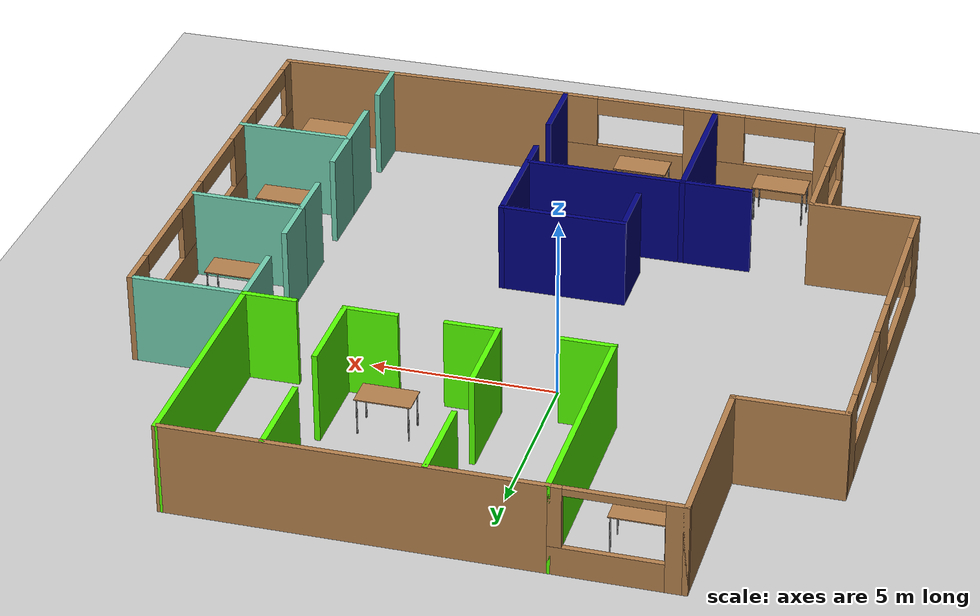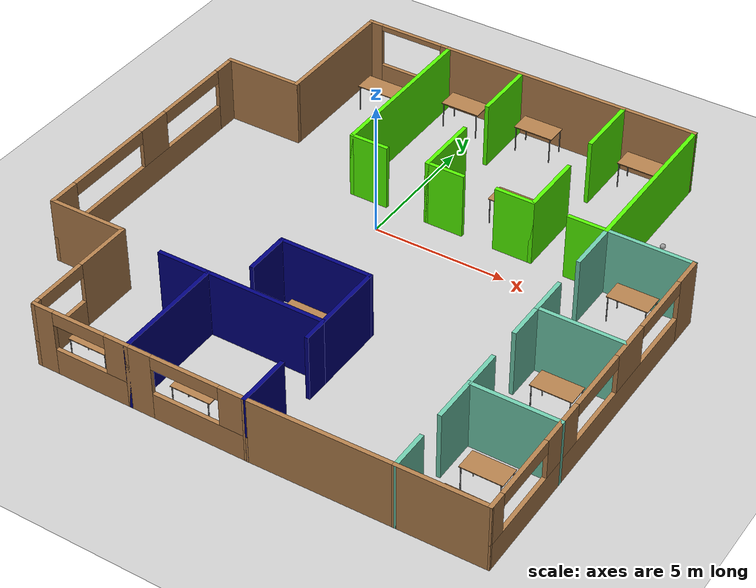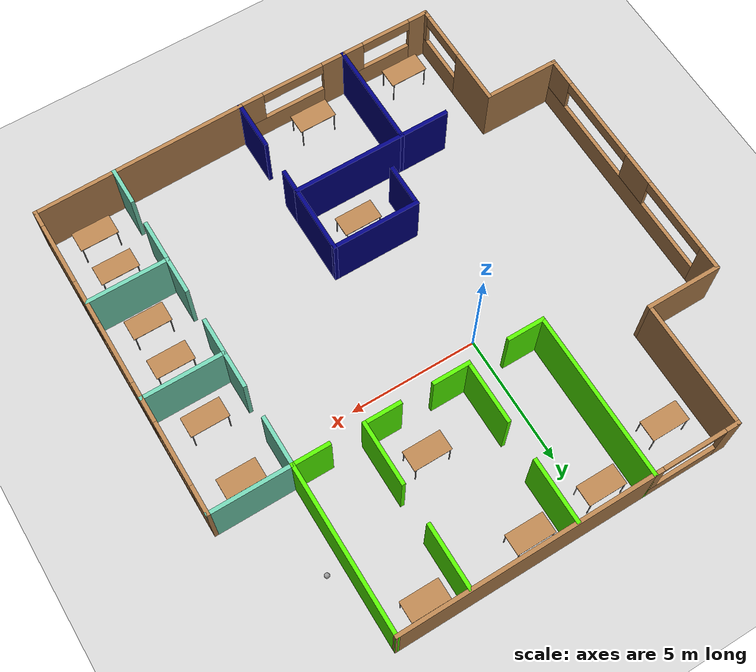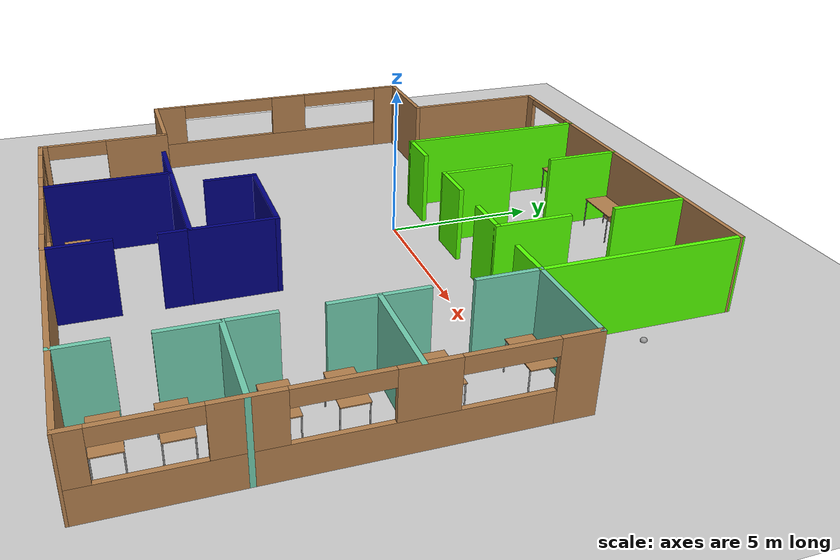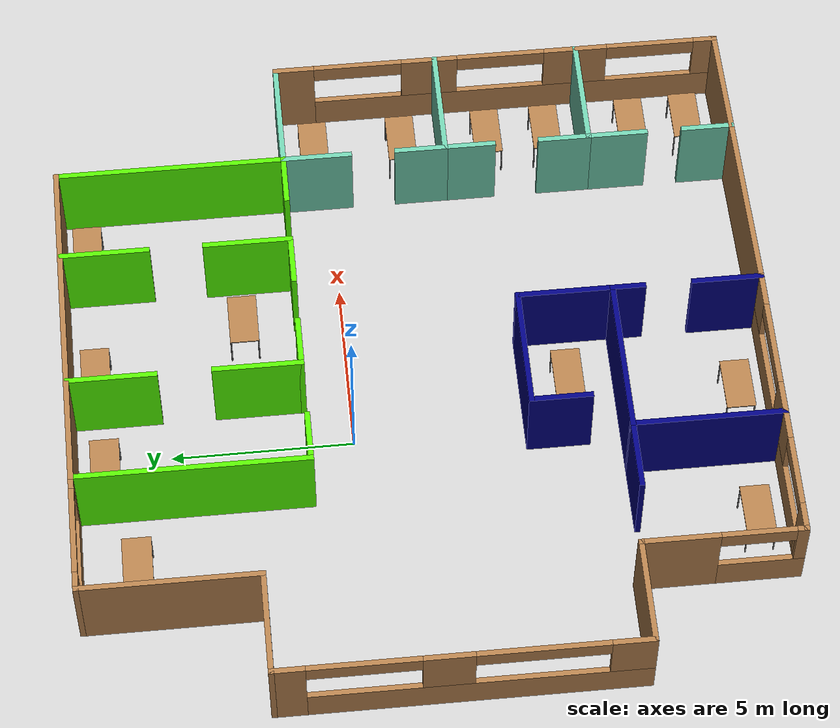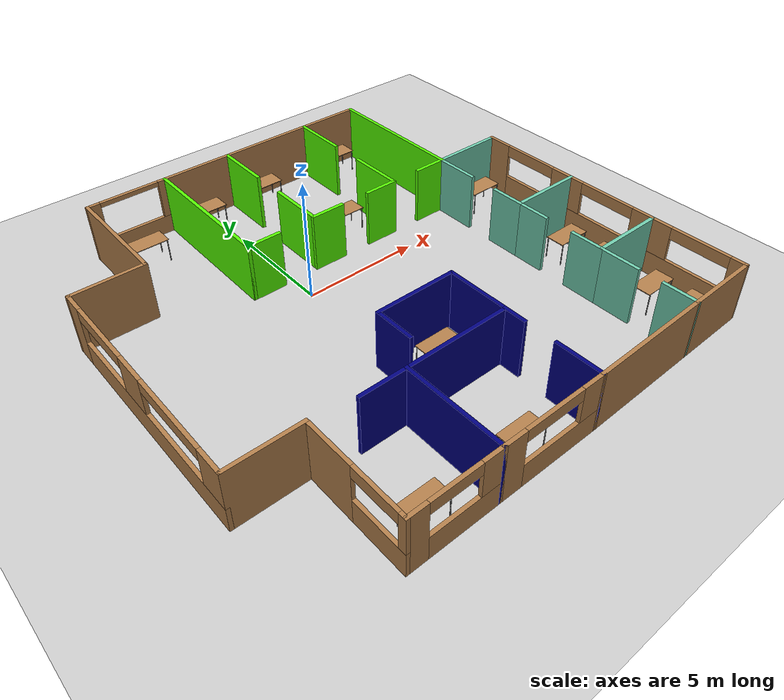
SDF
<sdf version="1.6">
 <world name="default">
  <plugin name="welcome" filename="libwelcome.so"/>
  <light name="sun" type="directional">
   <pose>0 0 10 0 -0 0</pose>
   <diffuse>0.8 0.8 0.8 1</diffuse>
   <specular>0.2 0.2 0.2 1</specular>
   <attenuation>
    <range>1000</range>
    <constant>0.9</constant>
    <linear>0.01</linear>
    <quadratic>0.001</quadratic>
   </attenuation>
   <direction>-0.5 0.1 -0.9</direction>
  </light>
  <model name="ground_plane">
   <static>1</static>
   <link name="link">
    <collision name="collision">
     <geometry><plane><normal>0 0 1</normal><size>100 100</size></plane></geometry>
     <surface><friction><ode><mu>100</mu><mu2>50</mu2></ode></friction></surface>
    </collision>
    <visual name="visual">
     <cast_shadows>0</cast_shadows>
     <geometry><plane><normal>0 0 1</normal><size>100 100</size></plane></geometry>
     <material>
      <script><uri>file://media/materials/scripts/gazebo.material</uri><name>Gazebo/Grey</name></script>
     </material>
    </visual>
   </link>
  </model>
  <gravity>0 0 -9.8</gravity>
  <magnetic_field>6e-06 2.3e-05 -4.2e-05</magnetic_field>
  <atmosphere type="adiabatic"/>
  <physics name="default_physics" default="0" type="ode">
   <max_step_size>0.001</max_step_size>
   <real_time_factor>1</real_time_factor>
   <real_time_update_rate>1000</real_time_update_rate>
  </physics>
  <scene><ambient>0.4 0.4 0.4 1</ambient><background>0.7 0.7 0.7 1</background><shadows>1</shadows></scene>
  <spherical_coordinates>
   <surface_model>EARTH_WGS84</surface_model>
   <latitude_deg>0</latitude_deg>
   <longitude_deg>0</longitude_deg>
   <elevation>0</elevation>
   <heading_deg>0</heading_deg>
  </spherical_coordinates>
  <model name="Office_Building">
   <pose>1.54423 -1.89975 0 0 -0 0</pose>
   <link name="Wall_1">
    <pose>-4.9967 9.51095 0 0 -0 0</pose>
    <visual name="Wall_1_Visual_0">
     <pose>-1.46283 0 1.25 0 -0 0</pose>
     <geometry><box><size>0.574332 0.15 2.5</size></box></geometry>
     <material>
      <script><uri>file://media/materials/scripts/gazebo.material</uri><name>Gazebo/Wood</name></script>
      <ambient>1 1 1 1</ambient>
     </material>
     <meta><layer>0</layer></meta>
    </visual>
    <collision name="Wall_1_Collision_0">
     <geometry><box><size>0.574332 0.15 2.5</size></box></geometry>
     <pose>-1.46283 0 1.25 0 -0 0</pose>
    </collision>
    <visual name="Wall_1_Visual_1">
     <pose>0.287166 0 0.4 0 -0 0</pose>
     <geometry><box><size>2.92567 0.15 0.8</size></box></geometry>
     <material>
      <script><uri>file://media/materials/scripts/gazebo.material</uri><name>Gazebo/Wood</name></script>
      <ambient>1 1 1 1</ambient>
     </material>
     <meta><layer>0</layer></meta>
    </visual>
    <collision name="Wall_1_Collision_1">
     <geometry><box><size>2.92567 0.15 0.8</size></box></geometry>
     <pose>0.287166 0 0.4 0 -0 0</pose>
    </collision>
    <visual name="Wall_1_Visual_2">
     <pose>1.53717 0 1.65 0 -0 0</pose>
     <geometry><box><size>0.425668 0.15 1.7</size></box></geometry>
     <material>
      <script><uri>file://media/materials/scripts/gazebo.material</uri><name>Gazebo/Wood</name></script>
      <ambient>1 1 1 1</ambient>
     </material>
     <meta><layer>0</layer></meta>
    </visual>
    <collision name="Wall_1_Collision_2">
     <geometry><box><size>0.425668 0.15 1.7</size></box></geometry>
     <pose>1.53717 0 1.65 0 -0 0</pose>
    </collision>
    <visual name="Wall_1_Visual_3">
     <pose>0.074332 0 2.4 0 -0 0</pose>
     <geometry><box><size>2.5 0.15 0.2</size></box></geometry>
     <material>
      <script><uri>file://media/materials/scripts/gazebo.material</uri><name>Gazebo/Wood</name></script>
      <ambient>1 1 1 1</ambient>
     </material>
     <meta><layer>0</layer></meta>
    </visual>
    <collision name="Wall_1_Collision_3">
     <geometry><box><size>2.5 0.15 0.2</size></box></geometry>
     <pose>0.074332 0 2.4 0 -0 0</pose>
    </collision>
   </link>
   <link name="Wall_12">
    <collision name="Wall_12_Collision">
     <geometry><box><size>1.5 0.15 2.5</size></box></geometry>
     <pose>0 0 1.25 0 -0 0</pose>
    </collision>
    <visual name="Wall_12_Visual">
     <pose>0 0 1.25 0 -0 0</pose>
     <geometry><box><size>1.5 0.15 2.5</size></box></geometry>
     <material>
      <script><uri>file://media/materials/scripts/gazebo.material</uri><name>Gazebo/Grey</name></script>
      <ambient>0.333333 1 0 1</ambient>
     </material>
     <meta><layer>0</layer></meta>
    </visual>
    <pose>0.345497 3.18997 0 0 -0 0</pose>
   </link>
   <link name="Wall_16">
    <collision name="Wall_16_Collision">
     <geometry><box><size>1.5 0.15 2.5</size></box></geometry>
     <pose>0 0 1.25 0 -0 0</pose>
    </collision>
    <visual name="Wall_16_Visual">
     <pose>0 0 1.25 0 -0 0</pose>
     <geometry><box><size>1.5 0.15 2.5</size></box></geometry>
     <material>
      <script><uri>file://media/materials/scripts/gazebo.material</uri><name>Gazebo/Grey</name></script>
      <ambient>0.333333 1 0 1</ambient>
     </material>
     <meta><layer>0</layer></meta>
    </visual>
    <pose>3.0455 3.18997 0 0 -0 0</pose>
   </link>
   <link name="Wall_18">
    <collision name="Wall_18_Collision">
     <geometry><box><size>1.5 0.15 2.5</size></box></geometry>
     <pose>0 0 1.25 0 -0 0</pose>
    </collision>
    <visual name="Wall_18_Visual">
     <pose>0 0 1.25 0 -0 0</pose>
     <geometry><box><size>1.5 0.15 2.5</size></box></geometry>
     <material>
      <script><uri>file://media/materials/scripts/gazebo.material</uri><name>Gazebo/Grey</name></script>
      <ambient>0.333333 1 0 1</ambient>
     </material>
     <meta><layer>0</layer></meta>
    </visual>
    <pose>5.7455 3.18997 0 0 -0 0</pose>
   </link>
   <link name="Wall_2">
    <collision name="Wall_2_Collision">
     <geometry><box><size>6.5 0.15 2.5</size></box></geometry>
     <pose>0 0 1.25 0 -0 0</pose>
    </collision>
    <visual name="Wall_2_Visual">
     <pose>0 0 1.25 0 -0 0</pose>
     <geometry><box><size>6.5 0.15 2.5</size></box></geometry>
     <material>
      <script><uri>file://media/materials/scripts/gazebo.material</uri><name>Gazebo/Grey</name></script>
      <ambient>0.333333 1 0 1</ambient>
     </material>
     <meta><layer>0</layer></meta>
    </visual>
    <pose>-3.3217 6.33595 0 0 0 -1.5708</pose>
   </link>
   <link name="Wall_22">
    <collision name="Wall_22_Collision">
     <geometry><box><size>6.5 0.15 2.5</size></box></geometry>
     <pose>0 0 1.25 0 -0 0</pose>
    </collision>
    <visual name="Wall_22_Visual">
     <pose>0 0 1.25 0 -0 0</pose>
     <geometry><box><size>6.5 0.15 2.5</size></box></geometry>
     <material>
      <script><uri>file://media/materials/scripts/gazebo.material</uri><name>Gazebo/Grey</name></script>
      <ambient>0.333333 1 0 1</ambient>
     </material>
     <meta><layer>0</layer></meta>
    </visual>
    <pose>6.4205 6.36497 0 0 -0 1.5708</pose>
   </link>
   <link name="Wall_23">
    <collision name="Wall_23_Collision">
     <geometry><box><size>9.89224 0.15 2.5</size></box></geometry>
     <pose>0 0 1.25 0 -0 0</pose>
    </collision>
    <visual name="Wall_23_Visual">
     <pose>0 0 1.25 0 -0 0</pose>
     <geometry><box><size>9.89224 0.15 2.5</size></box></geometry>
     <material>
      <script><uri>file://media/materials/scripts/gazebo.material</uri><name>Gazebo/Wood</name></script>
      <ambient>1 1 1 1</ambient>
     </material>
     <meta><layer>0</layer></meta>
    </visual>
    <pose>1.5494 9.52546 0 0 0 -3.13861</pose>
   </link>
   <link name="Wall_25">
    <collision name="Wall_25_Collision">
     <geometry><box><size>2.5 0.15 2.5</size></box></geometry>
     <pose>0 0 1.25 0 -0 0</pose>
    </collision>
    <visual name="Wall_25_Visual">
     <pose>0 0 1.25 0 -0 0</pose>
     <geometry><box><size>2.5 0.15 2.5</size></box></geometry>
     <material>
      <script><uri>file://media/materials/scripts/gazebo.material</uri><name>Gazebo/Grey</name></script>
      <ambient>0.333333 1 0 1</ambient>
     </material>
     <meta><layer>0</layer></meta>
    </visual>
    <pose>-0.329504 4.36497 0 0 -0 1.5708</pose>
   </link>
   <link name="Wall_3">
    <collision name="Wall_3_Collision">
     <geometry><box><size>1.5 0.15 2.5</size></box></geometry>
     <pose>0 0 1.25 0 -0 0</pose>
    </collision>
    <visual name="Wall_3_Visual">
     <pose>0 0 1.25 0 -0 0</pose>
     <geometry><box><size>1.5 0.15 2.5</size></box></geometry>
     <material>
      <script><uri>file://media/materials/scripts/gazebo.material</uri><name>Gazebo/Grey</name></script>
      <ambient>0.333333 1 0 1</ambient>
     </material>
     <meta><layer>0</layer></meta>
    </visual>
    <pose>-2.6467 3.16095 0 0 -0 0</pose>
   </link>
   <link name="Wall_30">
    <collision name="Wall_30_Collision">
     <geometry><box><size>2.5 0.15 2.5</size></box></geometry>
     <pose>0 0 1.25 0 -0 0</pose>
    </collision>
    <visual name="Wall_30_Visual">
     <pose>0 0 1.25 0 -0 0</pose>
     <geometry><box><size>2.5 0.15 2.5</size></box></geometry>
     <material>
      <script><uri>file://media/materials/scripts/gazebo.material</uri><name>Gazebo/Grey</name></script>
      <ambient>0.333333 1 0 1</ambient>
     </material>
     <meta><layer>0</layer></meta>
    </visual>
    <pose>-0.329504 8.31497 0 0 -0 1.5708</pose>
   </link>
   <link name="Wall_32">
    <collision name="Wall_32_Collision">
     <geometry><box><size>2.5 0.15 2.5</size></box></geometry>
     <pose>0 0 1.25 0 -0 0</pose>
    </collision>
    <visual name="Wall_32_Visual">
     <pose>0 0 1.25 0 -0 0</pose>
     <geometry><box><size>2.5 0.15 2.5</size></box></geometry>
     <material>
      <script><uri>file://media/materials/scripts/gazebo.material</uri><name>Gazebo/Grey</name></script>
      <ambient>0.333333 1 0 1</ambient>
     </material>
     <meta><layer>0</layer></meta>
    </visual>
    <pose>3.7205 4.36497 0 0 -0 1.5708</pose>
   </link>
   <link name="Wall_36">
    <collision name="Wall_36_Collision">
     <geometry><box><size>2.5 0.15 2.5</size></box></geometry>
     <pose>0 0 1.25 0 -0 0</pose>
    </collision>
    <visual name="Wall_36_Visual">
     <pose>0 0 1.25 0 -0 0</pose>
     <geometry><box><size>2.5 0.15 2.5</size></box></geometry>
     <material>
      <script><uri>file://media/materials/scripts/gazebo.material</uri><name>Gazebo/Grey</name></script>
      <ambient>0.333333 1 0 1</ambient>
     </material>
     <meta><layer>0</layer></meta>
    </visual>
    <pose>3.7205 8.31497 0 0 -0 1.5708</pose>
   </link>
   <link name="Wall_45">
    <pose>-9.5217 -0.264053 0 0 0 -1.5708</pose>
    <visual name="Wall_45_Visual_0">
     <pose>-4.52501 0 1.25 0 -0 0</pose>
     <geometry><box><size>0.949979 0.15 2.5</size></box></geometry>
     <material>
      <script><uri>file://media/materials/scripts/gazebo.material</uri><name>Gazebo/Wood</name></script>
      <ambient>1 1 1 1</ambient>
     </material>
     <meta><layer>0</layer></meta>
    </visual>
    <collision name="Wall_45_Collision_0">
     <geometry><box><size>0.949979 0.15 2.5</size></box></geometry>
     <pose>-4.52501 0 1.25 0 -0 0</pose>
    </collision>
    <visual name="Wall_45_Visual_1">
     <pose>0.47499 0 0.5 0 -0 0</pose>
     <geometry><box><size>9.05002 0.15 1</size></box></geometry>
     <material>
      <script><uri>file://media/materials/scripts/gazebo.material</uri><name>Gazebo/Wood</name></script>
      <ambient>1 1 1 1</ambient>
     </material>
     <meta><layer>0</layer></meta>
    </visual>
    <collision name="Wall_45_Collision_1">
     <geometry><box><size>9.05002 0.15 1</size></box></geometry>
     <pose>0.47499 0 0.5 0 -0 0</pose>
    </collision>
    <visual name="Wall_45_Visual_2">
     <pose>-0.367725 0 1.75 0 -0 0</pose>
     <geometry><box><size>1.36459 0.15 1.5</size></box></geometry>
     <material>
      <script><uri>file://media/materials/scripts/gazebo.material</uri><name>Gazebo/Wood</name></script>
      <ambient>1 1 1 1</ambient>
     </material>
     <meta><layer>0</layer></meta>
    </visual>
    <collision name="Wall_45_Collision_2">
     <geometry><box><size>1.36459 0.15 1.5</size></box></geometry>
     <pose>-0.367725 0 1.75 0 -0 0</pose>
    </collision>
    <visual name="Wall_45_Visual_3">
     <pose>4.40728 0 1.75 0 -0 0</pose>
     <geometry><box><size>1.18543 0.15 1.5</size></box></geometry>
     <material>
      <script><uri>file://media/materials/scripts/gazebo.material</uri><name>Gazebo/Wood</name></script>
      <ambient>1 1 1 1</ambient>
     </material>
     <meta><layer>0</layer></meta>
    </visual>
    <collision name="Wall_45_Collision_3">
     <geometry><box><size>1.18543 0.15 1.5</size></box></geometry>
     <pose>4.40728 0 1.75 0 -0 0</pose>
    </collision>
    <visual name="Wall_45_Visual_4">
     <pose>-2.55002 0 2.25 0 -0 0</pose>
     <geometry><box><size>3 0.15 0.5</size></box></geometry>
     <material>
      <script><uri>file://media/materials/scripts/gazebo.material</uri><name>Gazebo/Wood</name></script>
      <ambient>1 1 1 1</ambient>
     </material>
     <meta><layer>0</layer></meta>
    </visual>
    <collision name="Wall_45_Collision_4">
     <geometry><box><size>3 0.15 0.5</size></box></geometry>
     <pose>-2.55002 0 2.25 0 -0 0</pose>
    </collision>
    <visual name="Wall_45_Visual_5">
     <pose>2.06457 0 2.25 0 -0 0</pose>
     <geometry><box><size>3.5 0.15 0.5</size></box></geometry>
     <material>
      <script><uri>file://media/materials/scripts/gazebo.material</uri><name>Gazebo/Wood</name></script>
      <ambient>1 1 1 1</ambient>
     </material>
     <meta><layer>0</layer></meta>
    </visual>
    <collision name="Wall_45_Collision_5">
     <geometry><box><size>3.5 0.15 0.5</size></box></geometry>
     <pose>2.06457 0 2.25 0 -0 0</pose>
    </collision>
   </link>
   <link name="Wall_46">
    <collision name="Wall_46_Collision">
     <geometry><box><size>3 0.15 2.5</size></box></geometry>
     <pose>0 0 1.25 0 -0 0</pose>
    </collision>
    <visual name="Wall_46_Visual">
     <pose>0 0 1.25 0 -0 0</pose>
     <geometry><box><size>3 0.15 2.5</size></box></geometry>
     <material>
      <script><uri>file://media/materials/scripts/gazebo.material</uri><name>Gazebo/Wood</name></script>
      <ambient>1 1 1 1</ambient>
     </material>
     <meta><layer>0</layer></meta>
    </visual>
    <pose>-8.0967 -5.18905 0 0 -0 0</pose>
   </link>
   <link name="Wall_48">
    <pose>-6.6717 -7.36405 0 0 0 -1.5708</pose>
    <visual name="Wall_48_Visual_0">
     <pose>-1.15861 0 1.25 0 -0 0</pose>
     <geometry><box><size>2.18277 0.15 2.5</size></box></geometry>
     <material>
      <script><uri>file://media/materials/scripts/gazebo.material</uri><name>Gazebo/Wood</name></script>
      <ambient>0 0 0.498039 1</ambient>
     </material>
     <meta><layer>0</layer></meta>
    </visual>
    <collision name="Wall_48_Collision_0">
     <geometry><box><size>2.18277 0.15 2.5</size></box></geometry>
     <pose>-1.15861 0 1.25 0 -0 0</pose>
    </collision>
    <visual name="Wall_48_Visual_1">
     <pose>1.09139 0 0.5 0 -0 0</pose>
     <geometry><box><size>2.31723 0.15 1</size></box></geometry>
     <material>
      <script><uri>file://media/materials/scripts/gazebo.material</uri><name>Gazebo/Wood</name></script>
      <ambient>0 0 0.498039 1</ambient>
     </material>
     <meta><layer>0</layer></meta>
    </visual>
    <collision name="Wall_48_Collision_1">
     <geometry><box><size>2.31723 0.15 1</size></box></geometry>
     <pose>1.09139 0 0.5 0 -0 0</pose>
    </collision>
    <visual name="Wall_48_Visual_2">
     <pose>2.09139 0 1.75 0 -0 0</pose>
     <geometry><box><size>0.317226 0.15 1.5</size></box></geometry>
     <material>
      <script><uri>file://media/materials/scripts/gazebo.material</uri><name>Gazebo/Wood</name></script>
      <ambient>0 0 0.498039 1</ambient>
     </material>
     <meta><layer>0</layer></meta>
    </visual>
    <collision name="Wall_48_Collision_2">
     <geometry><box><size>0.317226 0.15 1.5</size></box></geometry>
     <pose>2.09139 0 1.75 0 -0 0</pose>
    </collision>
    <visual name="Wall_48_Visual_3">
     <pose>0.932774 0 2.25 0 -0 0</pose>
     <geometry><box><size>2 0.15 0.5</size></box></geometry>
     <material>
      <script><uri>file://media/materials/scripts/gazebo.material</uri><name>Gazebo/Wood</name></script>
      <ambient>0 0 0.498039 1</ambient>
     </material>
     <meta><layer>0</layer></meta>
    </visual>
    <collision name="Wall_48_Collision_3">
     <geometry><box><size>2 0.15 0.5</size></box></geometry>
     <pose>0.932774 0 2.25 0 -0 0</pose>
    </collision>
   </link>
   <link name="Wall_49">
    <pose>-4.8717 -9.53905 0 0 -0 0</pose>
    <visual name="Wall_49_Visual_0">
     <pose>-1.4581 0 1.25 0 -0 0</pose>
     <geometry><box><size>0.833803 0.15 2.5</size></box></geometry>
     <material>
      <script><uri>file://media/materials/scripts/gazebo.material</uri><name>Gazebo/Wood</name></script>
      <ambient>0 0 0.498039 1</ambient>
     </material>
     <meta><layer>0</layer></meta>
    </visual>
    <collision name="Wall_49_Collision_0">
     <geometry><box><size>0.833803 0.15 2.5</size></box></geometry>
     <pose>-1.4581 0 1.25 0 -0 0</pose>
    </collision>
    <visual name="Wall_49_Visual_1">
     <pose>0.416901 0 0.5 0 -0 0</pose>
     <geometry><box><size>2.9162 0.15 1</size></box></geometry>
     <material>
      <script><uri>file://media/materials/scripts/gazebo.material</uri><name>Gazebo/Wood</name></script>
      <ambient>0 0 0.498039 1</ambient>
     </material>
     <meta><layer>0</layer></meta>
    </visual>
    <collision name="Wall_49_Collision_1">
     <geometry><box><size>2.9162 0.15 1</size></box></geometry>
     <pose>0.416901 0 0.5 0 -0 0</pose>
    </collision>
    <visual name="Wall_49_Visual_2">
     <pose>1.4169 0 1.75 0 -0 0</pose>
     <geometry><box><size>0.916197 0.15 1.5</size></box></geometry>
     <material>
      <script><uri>file://media/materials/scripts/gazebo.material</uri><name>Gazebo/Wood</name></script>
      <ambient>0 0 0.498039 1</ambient>
     </material>
     <meta><layer>0</layer></meta>
    </visual>
    <collision name="Wall_49_Collision_2">
     <geometry><box><size>0.916197 0.15 1.5</size></box></geometry>
     <pose>1.4169 0 1.75 0 -0 0</pose>
    </collision>
    <visual name="Wall_49_Visual_3">
     <pose>-0.041197 0 2.25 0 -0 0</pose>
     <geometry><box><size>2 0.15 0.5</size></box></geometry>
     <material>
      <script><uri>file://media/materials/scripts/gazebo.material</uri><name>Gazebo/Wood</name></script>
      <ambient>0 0 0.498039 1</ambient>
     </material>
     <meta><layer>0</layer></meta>
    </visual>
    <collision name="Wall_49_Collision_3">
     <geometry><box><size>2 0.15 0.5</size></box></geometry>
     <pose>-0.041197 0 2.25 0 -0 0</pose>
    </collision>
   </link>
   <link name="Wall_50">
    <collision name="Wall_50_Collision">
     <geometry><box><size>4.25 0.15 2.5</size></box></geometry>
     <pose>0 0 1.25 0 -0 0</pose>
    </collision>
    <visual name="Wall_50_Visual">
     <pose>0 0 1.25 0 -0 0</pose>
     <geometry><box><size>4.25 0.15 2.5</size></box></geometry>
     <material>
      <script><uri>file://media/materials/scripts/gazebo.material</uri><name>Gazebo/Grey</name></script>
      <ambient>0 0 0.498039 1</ambient>
     </material>
     <meta><layer>0</layer></meta>
    </visual>
    <pose>-3.0717 -7.48905 0 0 -0 1.5708</pose>
   </link>
   <link name="Wall_51">
    <collision name="Wall_51_Collision">
     <geometry><box><size>4.5 0.15 2.5</size></box></geometry>
     <pose>0 0 1.25 0 -0 0</pose>
    </collision>
    <visual name="Wall_51_Visual">
     <pose>0 0 1.25 0 -0 0</pose>
     <geometry><box><size>4.5 0.15 2.5</size></box></geometry>
     <material>
      <script><uri>file://media/materials/scripts/gazebo.material</uri><name>Gazebo/Grey</name></script>
      <ambient>0 0 0.498039 1</ambient>
     </material>
     <meta><layer>0</layer></meta>
    </visual>
    <pose>-0.896696 -5.43905 0 0 -0 0</pose>
   </link>
   <link name="Wall_52">
    <collision name="Wall_52_Collision">
     <geometry><box><size>2.75 0.15 2.5</size></box></geometry>
     <pose>0 0 1.25 0 -0 0</pose>
    </collision>
    <visual name="Wall_52_Visual">
     <pose>0 0 1.25 0 -0 0</pose>
     <geometry><box><size>2.75 0.15 2.5</size></box></geometry>
     <material>
      <script><uri>file://media/materials/scripts/gazebo.material</uri><name>Gazebo/Grey</name></script>
      <ambient>0 0 0.498039 1</ambient>
     </material>
     <meta><layer>0</layer></meta>
    </visual>
    <pose>1.2783 -4.13905 0 0 -0 1.5708</pose>
   </link>
   <link name="Wall_53">
    <collision name="Wall_53_Collision">
     <geometry><box><size>3.5 0.15 2.5</size></box></geometry>
     <pose>0 0 1.25 0 -0 0</pose>
    </collision>
    <visual name="Wall_53_Visual">
     <pose>0 0 1.25 0 -0 0</pose>
     <geometry><box><size>3.5 0.15 2.5</size></box></geometry>
     <material>
      <script><uri>file://media/materials/scripts/gazebo.material</uri><name>Gazebo/Grey</name></script>
      <ambient>0 0 0.498039 1</ambient>
     </material>
     <meta><layer>0</layer></meta>
    </visual>
    <pose>-0.396696 -2.83905 0 0 -0 3.14159</pose>
   </link>
   <link name="Wall_54">
    <collision name="Wall_54_Collision">
     <geometry><box><size>1.75 0.15 2.5</size></box></geometry>
     <pose>0 0 1.25 0 -0 0</pose>
    </collision>
    <visual name="Wall_54_Visual">
     <pose>0 0 1.25 0 -0 0</pose>
     <geometry><box><size>1.75 0.15 2.5</size></box></geometry>
     <material>
      <script><uri>file://media/materials/scripts/gazebo.material</uri><name>Gazebo/Grey</name></script>
      <ambient>0 0 0.498039 1</ambient>
     </material>
     <meta><layer>0</layer></meta>
    </visual>
    <pose>-2.0717 -3.63905 0 0 0 -1.5708</pose>
   </link>
   <link name="Wall_56">
    <collision name="Wall_56_Collision">
     <geometry><box><size>2 0.15 2.5</size></box></geometry>
     <pose>0 0 1.25 0 -0 0</pose>
    </collision>
    <visual name="Wall_56_Visual">
     <pose>0 0 1.25 0 -0 0</pose>
     <geometry><box><size>2 0.15 2.5</size></box></geometry>
     <material>
      <script><uri>file://media/materials/scripts/gazebo.material</uri><name>Gazebo/Grey</name></script>
      <ambient>0 0 0.498039 1</ambient>
     </material>
     <meta><layer>0</layer></meta>
    </visual>
    <pose>-3.9967 -5.43905 0 0 -0 3.14159</pose>
   </link>
   <link name="Wall_59">
    <pose>-0.896696 -9.53905 0 0 -0 0</pose>
    <visual name="Wall_59_Visual_0">
     <pose>-1.75844 0 1.25 0 -0 0</pose>
     <geometry><box><size>0.983115 0.15 2.5</size></box></geometry>
     <material>
      <script><uri>file://media/materials/scripts/gazebo.material</uri><name>Gazebo/Wood</name></script>
      <ambient>0 0 0.498039 1</ambient>
     </material>
     <meta><layer>0</layer></meta>
    </visual>
    <collision name="Wall_59_Collision_0">
     <geometry><box><size>0.983115 0.15 2.5</size></box></geometry>
     <pose>-1.75844 0 1.25 0 -0 0</pose>
    </collision>
    <visual name="Wall_59_Visual_1">
     <pose>0.491557 0 0.5 0 -0 0</pose>
     <geometry><box><size>3.51688 0.15 1</size></box></geometry>
     <material>
      <script><uri>file://media/materials/scripts/gazebo.material</uri><name>Gazebo/Wood</name></script>
      <ambient>0 0 0.498039 1</ambient>
     </material>
     <meta><layer>0</layer></meta>
    </visual>
    <collision name="Wall_59_Collision_1">
     <geometry><box><size>3.51688 0.15 1</size></box></geometry>
     <pose>0.491557 0 0.5 0 -0 0</pose>
    </collision>
    <visual name="Wall_59_Visual_2">
     <pose>1.74156 0 1.75 0 -0 0</pose>
     <geometry><box><size>1.01689 0.15 1.5</size></box></geometry>
     <material>
      <script><uri>file://media/materials/scripts/gazebo.material</uri><name>Gazebo/Wood</name></script>
      <ambient>0 0 0.498039 1</ambient>
     </material>
     <meta><layer>0</layer></meta>
    </visual>
    <collision name="Wall_59_Collision_2">
     <geometry><box><size>1.01689 0.15 1.5</size></box></geometry>
     <pose>1.74156 0 1.75 0 -0 0</pose>
    </collision>
    <visual name="Wall_59_Visual_3">
     <pose>-0.016885 0 2.25 0 -0 0</pose>
     <geometry><box><size>2.5 0.15 0.5</size></box></geometry>
     <material>
      <script><uri>file://media/materials/scripts/gazebo.material</uri><name>Gazebo/Wood</name></script>
      <ambient>0 0 0.498039 1</ambient>
     </material>
     <meta><layer>0</layer></meta>
    </visual>
    <collision name="Wall_59_Collision_3">
     <geometry><box><size>2.5 0.15 0.5</size></box></geometry>
     <pose>-0.016885 0 2.25 0 -0 0</pose>
    </collision>
   </link>
   <link name="Wall_60">
    <collision name="Wall_60_Collision">
     <geometry><box><size>2 0.15 2.5</size></box></geometry>
     <pose>0 0 1.25 0 -0 0</pose>
    </collision>
    <visual name="Wall_60_Visual">
     <pose>0 0 1.25 0 -0 0</pose>
     <geometry><box><size>2 0.15 2.5</size></box></geometry>
     <material>
      <script><uri>file://media/materials/scripts/gazebo.material</uri><name>Gazebo/Grey</name></script>
      <ambient>0 0 0.498039 1</ambient>
     </material>
     <meta><layer>0</layer></meta>
    </visual>
    <pose>1.2783 -8.61405 0 0 -0 1.5708</pose>
   </link>
   <link name="Wall_63">
    <collision name="Wall_63_Collision">
     <geometry><box><size>1 0.15 2.5</size></box></geometry>
     <pose>0 0 1.25 0 -0 0</pose>
    </collision>
    <visual name="Wall_63_Visual">
     <pose>0 0 1.25 0 -0 0</pose>
     <geometry><box><size>1 0.15 2.5</size></box></geometry>
     <material>
      <script><uri>file://media/materials/scripts/gazebo.material</uri><name>Gazebo/Grey</name></script>
      <ambient>0 0 0.498039 1</ambient>
     </material>
     <meta><layer>0</layer></meta>
    </visual>
    <pose>1.2783 -5.86405 0 0 0 -1.5708</pose>
   </link>
   <link name="Wall_65">
    <collision name="Wall_65_Collision">
     <geometry><box><size>3.25 0.15 2.5</size></box></geometry>
     <pose>0 0 1.25 0 -0 0</pose>
    </collision>
    <visual name="Wall_65_Visual">
     <pose>0 0 1.25 0 -0 0</pose>
     <geometry><box><size>3.25 0.15 2.5</size></box></geometry>
     <material>
      <script><uri>file://media/materials/scripts/gazebo.material</uri><name>Gazebo/Grey</name></script>
      <ambient>0.435294 0.796078 0.67451 1</ambient>
     </material>
     <meta><layer>0</layer></meta>
    </visual>
    <pose>7.9705 3.18997 0 0 -0 0</pose>
   </link>
   <link name="Wall_66">
    <pose>9.5205 -3.11003 0 0 0 -1.5708</pose>
    <visual name="Wall_66_Visual_0">
     <pose>-5.79185 0 1.25 0 -0 0</pose>
     <geometry><box><size>1.1663 0.15 2.5</size></box></geometry>
     <material>
      <script><uri>file://media/materials/scripts/gazebo.material</uri><name>Gazebo/Wood</name></script>
      <ambient>0.435294 0.796078 0.67451 1</ambient>
     </material>
     <meta><layer>0</layer></meta>
    </visual>
    <collision name="Wall_66_Collision_0">
     <geometry><box><size>1.1663 0.15 2.5</size></box></geometry>
     <pose>-5.79185 0 1.25 0 -0 0</pose>
    </collision>
    <visual name="Wall_66_Visual_1">
     <pose>0.583151 0 0.5 0 -0 0</pose>
     <geometry><box><size>11.5837 0.15 1</size></box></geometry>
     <material>
      <script><uri>file://media/materials/scripts/gazebo.material</uri><name>Gazebo/Wood</name></script>
      <ambient>0.435294 0.796078 0.67451 1</ambient>
     </material>
     <meta><layer>0</layer></meta>
    </visual>
    <collision name="Wall_66_Collision_1">
     <geometry><box><size>11.5837 0.15 1</size></box></geometry>
     <pose>0.583151 0 0.5 0 -0 0</pose>
    </collision>
    <visual name="Wall_66_Visual_2">
     <pose>-1.90874 0 1.75 0 -0 0</pose>
     <geometry><box><size>1.59992 0.15 1.5</size></box></geometry>
     <material>
      <script><uri>file://media/materials/scripts/gazebo.material</uri><name>Gazebo/Wood</name></script>
      <ambient>0.435294 0.796078 0.67451 1</ambient>
     </material>
     <meta><layer>0</layer></meta>
    </visual>
    <collision name="Wall_66_Collision_2">
     <geometry><box><size>1.59992 0.15 1.5</size></box></geometry>
     <pose>-1.90874 0 1.75 0 -0 0</pose>
    </collision>
    <visual name="Wall_66_Visual_3">
     <pose>2.29484 0 1.75 0 -0 0</pose>
     <geometry><box><size>1.80724 0.15 1.5</size></box></geometry>
     <material>
      <script><uri>file://media/materials/scripts/gazebo.material</uri><name>Gazebo/Wood</name></script>
      <ambient>0.435294 0.796078 0.67451 1</ambient>
     </material>
     <meta><layer>0</layer></meta>
    </visual>
    <collision name="Wall_66_Collision_3">
     <geometry><box><size>1.80724 0.15 1.5</size></box></geometry>
     <pose>2.29484 0 1.75 0 -0 0</pose>
    </collision>
    <visual name="Wall_66_Visual_4">
     <pose>6.03673 0 1.75 0 -0 0</pose>
     <geometry><box><size>0.676535 0.15 1.5</size></box></geometry>
     <material>
      <script><uri>file://media/materials/scripts/gazebo.material</uri><name>Gazebo/Wood</name></script>
      <ambient>0.435294 0.796078 0.67451 1</ambient>
     </material>
     <meta><layer>0</layer></meta>
    </visual>
    <collision name="Wall_66_Collision_4">
     <geometry><box><size>0.676535 0.15 1.5</size></box></geometry>
     <pose>6.03673 0 1.75 0 -0 0</pose>
    </collision>
    <visual name="Wall_66_Visual_5">
     <pose>-3.9587 0 2.25 0 -0 0</pose>
     <geometry><box><size>2.5 0.15 0.5</size></box></geometry>
     <material>
      <script><uri>file://media/materials/scripts/gazebo.material</uri><name>Gazebo/Wood</name></script>
      <ambient>0.435294 0.796078 0.67451 1</ambient>
     </material>
     <meta><layer>0</layer></meta>
    </visual>
    <collision name="Wall_66_Collision_5">
     <geometry><box><size>2.5 0.15 0.5</size></box></geometry>
     <pose>-3.9587 0 2.25 0 -0 0</pose>
    </collision>
    <visual name="Wall_66_Visual_6">
     <pose>0.141222 0 2.25 0 -0 0</pose>
     <geometry><box><size>2.5 0.15 0.5</size></box></geometry>
     <material>
      <script><uri>file://media/materials/scripts/gazebo.material</uri><name>Gazebo/Wood</name></script>
      <ambient>0.435294 0.796078 0.67451 1</ambient>
     </material>
     <meta><layer>0</layer></meta>
    </visual>
    <collision name="Wall_66_Collision_6">
     <geometry><box><size>2.5 0.15 0.5</size></box></geometry>
     <pose>0.141222 0 2.25 0 -0 0</pose>
    </collision>
    <visual name="Wall_66_Visual_7">
     <pose>4.44846 0 2.25 0 -0 0</pose>
     <geometry><box><size>2.5 0.15 0.5</size></box></geometry>
     <material>
      <script><uri>file://media/materials/scripts/gazebo.material</uri><name>Gazebo/Wood</name></script>
      <ambient>0.435294 0.796078 0.67451 1</ambient>
     </material>
     <meta><layer>0</layer></meta>
    </visual>
    <collision name="Wall_66_Collision_7">
     <geometry><box><size>2.5 0.15 0.5</size></box></geometry>
     <pose>4.44846 0 2.25 0 -0 0</pose>
    </collision>
   </link>
   <link name="Wall_69">
    <collision name="Wall_69_Collision">
     <geometry><box><size>2 0.15 2.5</size></box></geometry>
     <pose>0 0 1.25 0 -0 0</pose>
    </collision>
    <visual name="Wall_69_Visual">
     <pose>0 0 1.25 0 -0 0</pose>
     <geometry><box><size>2 0.15 2.5</size></box></geometry>
     <material>
      <script><uri>file://media/materials/scripts/gazebo.material</uri><name>Gazebo/Grey</name></script>
      <ambient>0.435294 0.796078 0.67451 1</ambient>
     </material>
     <meta><layer>0</layer></meta>
    </visual>
    <pose>6.4205 2.26497 0 0 0 -1.5708</pose>
   </link>
   <link name="Wall_7">
    <collision name="Wall_7_Collision">
     <geometry><box><size>5 0.15 2.5</size></box></geometry>
     <pose>0 0 1.25 0 -0 0</pose>
    </collision>
    <visual name="Wall_7_Visual">
     <pose>0 0 1.25 0 -0 0</pose>
     <geometry><box><size>5 0.15 2.5</size></box></geometry>
     <material>
      <script><uri>file://media/materials/scripts/gazebo.material</uri><name>Gazebo/Wood</name></script>
      <ambient>1 1 1 1</ambient>
     </material>
     <meta><layer>0</layer></meta>
    </visual>
    <pose>-6.6717 7.08595 0 0 0 -1.5708</pose>
   </link>
   <link name="Wall_75">
    <collision name="Wall_75_Collision">
     <geometry><box><size>1.5 0.15 2.5</size></box></geometry>
     <pose>0 0 1.25 0 -0 0</pose>
    </collision>
    <visual name="Wall_75_Visual">
     <pose>0 0 1.25 0 -0 0</pose>
     <geometry><box><size>1.5 0.15 2.5</size></box></geometry>
     <material>
      <script><uri>file://media/materials/scripts/gazebo.material</uri><name>Gazebo/Grey</name></script>
      <ambient>0.435294 0.796078 0.67451 1</ambient>
     </material>
     <meta><layer>0</layer></meta>
    </visual>
    <pose>6.4205 -0.685027 0 0 0 -1.5708</pose>
   </link>
   <link name="Wall_76">
    <collision name="Wall_76_Collision">
     <geometry><box><size>3.25 0.15 2.5</size></box></geometry>
     <pose>0 0 1.25 0 -0 0</pose>
    </collision>
    <visual name="Wall_76_Visual">
     <pose>0 0 1.25 0 -0 0</pose>
     <geometry><box><size>3.25 0.15 2.5</size></box></geometry>
     <material>
      <script><uri>file://media/materials/scripts/gazebo.material</uri><name>Gazebo/Grey</name></script>
      <ambient>0.435294 0.796078 0.67451 1</ambient>
     </material>
     <meta><layer>0</layer></meta>
    </visual>
    <pose>7.9705 -1.36003 0 0 -0 0</pose>
   </link>
   <link name="Wall_78">
    <collision name="Wall_78_Collision">
     <geometry><box><size>1.5 0.15 2.5</size></box></geometry>
     <pose>0 0 1.25 0 -0 0</pose>
    </collision>
    <visual name="Wall_78_Visual">
     <pose>0 0 1.25 0 -0 0</pose>
     <geometry><box><size>1.5 0.15 2.5</size></box></geometry>
     <material>
      <script><uri>file://media/materials/scripts/gazebo.material</uri><name>Gazebo/Grey</name></script>
      <ambient>0.435294 0.796078 0.67451 1</ambient>
     </material>
     <meta><layer>0</layer></meta>
    </visual>
    <pose>6.4205 -2.03503 0 0 0 -1.5708</pose>
   </link>
   <link name="Wall_8">
    <collision name="Wall_8_Collision">
     <geometry><box><size>3 0.15 2.5</size></box></geometry>
     <pose>0 0 1.25 0 -0 0</pose>
    </collision>
    <visual name="Wall_8_Visual">
     <pose>0 0 1.25 0 -0 0</pose>
     <geometry><box><size>3 0.15 2.5</size></box></geometry>
     <material>
      <script><uri>file://media/materials/scripts/gazebo.material</uri><name>Gazebo/Wood</name></script>
      <ambient>1 1 1 1</ambient>
     </material>
     <meta><layer>0</layer></meta>
    </visual>
    <pose>-8.0967 4.66095 0 0 -0 3.14159</pose>
   </link>
   <link name="Wall_80">
    <collision name="Wall_80_Collision">
     <geometry><box><size>1.5 0.15 2.5</size></box></geometry>
     <pose>0 0 1.25 0 -0 0</pose>
    </collision>
    <visual name="Wall_80_Visual">
     <pose>0 0 1.25 0 -0 0</pose>
     <geometry><box><size>1.5 0.15 2.5</size></box></geometry>
     <material>
      <script><uri>file://media/materials/scripts/gazebo.material</uri><name>Gazebo/Grey</name></script>
      <ambient>0.435294 0.796078 0.67451 1</ambient>
     </material>
     <meta><layer>0</layer></meta>
    </visual>
    <pose>6.4205 -4.73503 0 0 0 -1.5708</pose>
   </link>
   <link name="Wall_81">
    <collision name="Wall_81_Collision">
     <geometry><box><size>3.25 0.15 2.5</size></box></geometry>
     <pose>0 0 1.25 0 -0 0</pose>
    </collision>
    <visual name="Wall_81_Visual">
     <pose>0 0 1.25 0 -0 0</pose>
     <geometry><box><size>3.25 0.15 2.5</size></box></geometry>
     <material>
      <script><uri>file://media/materials/scripts/gazebo.material</uri><name>Gazebo/Grey</name></script>
      <ambient>0.435294 0.796078 0.67451 1</ambient>
     </material>
     <meta><layer>0</layer></meta>
    </visual>
    <pose>7.9705 -5.41003 0 0 -0 0</pose>
   </link>
   <link name="Wall_84">
    <collision name="Wall_84_Collision">
     <geometry><box><size>1.75 0.15 2.5</size></box></geometry>
     <pose>0 0 1.25 0 -0 0</pose>
    </collision>
    <visual name="Wall_84_Visual">
     <pose>0 0 1.25 0 -0 0</pose>
     <geometry><box><size>1.75 0.15 2.5</size></box></geometry>
     <material>
      <script><uri>file://media/materials/scripts/gazebo.material</uri><name>Gazebo/Grey</name></script>
      <ambient>0.435294 0.796078 0.67451 1</ambient>
     </material>
     <meta><layer>0</layer></meta>
    </visual>
    <pose>6.4205 -6.21003 0 0 0 -1.5708</pose>
   </link>
   <link name="Wall_88">
    <collision name="Wall_88_Collision">
     <geometry><box><size>1.5 0.15 2.5</size></box></geometry>
     <pose>0 0 1.25 0 -0 0</pose>
    </collision>
    <visual name="Wall_88_Visual">
     <pose>0 0 1.25 0 -0 0</pose>
     <geometry><box><size>1.5 0.15 2.5</size></box></geometry>
     <material>
      <script><uri>file://media/materials/scripts/gazebo.material</uri><name>Gazebo/Grey</name></script>
      <ambient>0.435294 0.796078 0.67451 1</ambient>
     </material>
     <meta><layer>0</layer></meta>
    </visual>
    <pose>6.4205 -8.78503 0 0 0 -1.5708</pose>
   </link>
   <link name="Wall_90">
    <collision name="Wall_90_Collision">
     <geometry><box><size>5.2928 0.15 2.5</size></box></geometry>
     <pose>0 0 1.25 0 -0 0</pose>
    </collision>
    <visual name="Wall_90_Visual">
     <pose>0 0 1.25 0 -0 0</pose>
     <geometry><box><size>5.2928 0.15 2.5</size></box></geometry>
     <material>
      <script><uri>file://media/materials/scripts/gazebo.material</uri><name>Gazebo/Wood</name></script>
      <ambient>1 1 1 1</ambient>
     </material>
     <meta><layer>0</layer></meta>
    </visual>
    <pose>3.8494 -9.49954 0 0 -0 0.015367</pose>
   </link>
   <link name="Wall_91">
    <collision name="Wall_91_Collision">
     <geometry><box><size>3.2504 0.15 2.5</size></box></geometry>
     <pose>0 0 1.25 0 -0 0</pose>
    </collision>
    <visual name="Wall_91_Visual">
     <pose>0 0 1.25 0 -0 0</pose>
     <geometry><box><size>3.2504 0.15 2.5</size></box></geometry>
     <material>
      <script><uri>file://media/materials/scripts/gazebo.material</uri><name>Gazebo/Wood</name></script>
      <ambient>0.435294 0.796078 0.67451 1</ambient>
     </material>
     <meta><layer>0</layer></meta>
    </visual>
    <pose>7.9705 -9.43503 0 0 -0 0.016128</pose>
   </link>
   <static>1</static>
  </model>
  <model name="table">
   <static>1</static>
   <link name="link">
    <collision name="surface">
     <pose>0 0 1 0 -0 0</pose>
     <geometry><box><size>1.5 0.8 0.03</size></box></geometry>
     <surface><friction><ode><mu>0.6</mu><mu2>0.6</mu2></ode></friction></surface>
    </collision>
    <visual name="visual1">
     <pose>0 0 1 0 -0 0</pose>
     <geometry><box><size>1.5 0.8 0.03</size></box></geometry>
     <material>
      <script><uri>file://media/materials/scripts/gazebo.material</uri><name>Gazebo/Wood</name></script>
     </material>
    </visual>
    <collision name="front_left_leg">
     <pose>0.68 0.38 0.5 0 -0 0</pose>
     <geometry><cylinder><radius>0.02</radius><length>1</length></cylinder></geometry>
    </collision>
    <visual name="front_left_leg">
     <pose>0.68 0.38 0.5 0 -0 0</pose>
     <geometry><cylinder><radius>0.02</radius><length>1</length></cylinder></geometry>
     <material>
      <script><uri>file://media/materials/scripts/gazebo.material</uri><name>Gazebo/Grey</name></script>
     </material>
    </visual>
    <collision name="front_right_leg">
     <pose>0.68 -0.38 0.5 0 -0 0</pose>
     <geometry><cylinder><radius>0.02</radius><length>1</length></cylinder></geometry>
    </collision>
    <visual name="front_right_leg">
     <pose>0.68 -0.38 0.5 0 -0 0</pose>
     <geometry><cylinder><radius>0.02</radius><length>1</length></cylinder></geometry>
     <material>
      <script><uri>file://media/materials/scripts/gazebo.material</uri><name>Gazebo/Grey</name></script>
     </material>
    </visual>
    <collision name="back_right_leg">
     <pose>-0.68 -0.38 0.5 0 -0 0</pose>
     <geometry><cylinder><radius>0.02</radius><length>1</length></cylinder></geometry>
    </collision>
    <visual name="back_right_leg">
     <pose>-0.68 -0.38 0.5 0 -0 0</pose>
     <geometry><cylinder><radius>0.02</radius><length>1</length></cylinder></geometry>
     <material>
      <script><uri>file://media/materials/scripts/gazebo.material</uri><name>Gazebo/Grey</name></script>
     </material>
    </visual>
    <collision name="back_left_leg">
     <pose>-0.68 0.38 0.5 0 -0 0</pose>
     <geometry><cylinder><radius>0.02</radius><length>1</length></cylinder></geometry>
    </collision>
    <visual name="back_left_leg">
     <pose>-0.68 0.38 0.5 0 -0 0</pose>
     <geometry><cylinder><radius>0.02</radius><length>1</length></cylinder></geometry>
     <material>
      <script><uri>file://media/materials/scripts/gazebo.material</uri><name>Gazebo/Grey</name></script>
     </material>
    </visual>
   </link>
   <pose>-0.561263 6.7633 0 0 -0 0</pose>
  </model>
  <model name="table_clone">
   <static>1</static>
   <link name="link">
    <collision name="surface">
     <pose>0 0 1 0 -0 0</pose>
     <geometry><box><size>1.5 0.8 0.03</size></box></geometry>
     <surface><friction><ode><mu>0.6</mu><mu2>0.6</mu2></ode></friction></surface>
    </collision>
    <visual name="visual1">
     <pose>0 0 1 0 -0 0</pose>
     <geometry><box><size>1.5 0.8 0.03</size></box></geometry>
     <material>
      <script><uri>file://media/materials/scripts/gazebo.material</uri><name>Gazebo/Wood</name></script>
     </material>
    </visual>
    <collision name="front_left_leg">
     <pose>0.68 0.38 0.5 0 -0 0</pose>
     <geometry><cylinder><radius>0.02</radius><length>1</length></cylinder></geometry>
    </collision>
    <visual name="front_left_leg">
     <pose>0.68 0.38 0.5 0 -0 0</pose>
     <geometry><cylinder><radius>0.02</radius><length>1</length></cylinder></geometry>
     <material>
      <script><uri>file://media/materials/scripts/gazebo.material</uri><name>Gazebo/Grey</name></script>
     </material>
    </visual>
    <collision name="front_right_leg">
     <pose>0.68 -0.38 0.5 0 -0 0</pose>
     <geometry><cylinder><radius>0.02</radius><length>1</length></cylinder></geometry>
    </collision>
    <visual name="front_right_leg">
     <pose>0.68 -0.38 0.5 0 -0 0</pose>
     <geometry><cylinder><radius>0.02</radius><length>1</length></cylinder></geometry>
     <material>
      <script><uri>file://media/materials/scripts/gazebo.material</uri><name>Gazebo/Grey</name></script>
     </material>
    </visual>
    <collision name="back_right_leg">
     <pose>-0.68 -0.38 0.5 0 -0 0</pose>
     <geometry><cylinder><radius>0.02</radius><length>1</length></cylinder></geometry>
    </collision>
    <visual name="back_right_leg">
     <pose>-0.68 -0.38 0.5 0 -0 0</pose>
     <geometry><cylinder><radius>0.02</radius><length>1</length></cylinder></geometry>
     <material>
      <script><uri>file://media/materials/scripts/gazebo.material</uri><name>Gazebo/Grey</name></script>
     </material>
    </visual>
    <collision name="back_left_leg">
     <pose>-0.68 0.38 0.5 0 -0 0</pose>
     <geometry><cylinder><radius>0.02</radius><length>1</length></cylinder></geometry>
    </collision>
    <visual name="back_left_leg">
     <pose>-0.68 0.38 0.5 0 -0 0</pose>
     <geometry><cylinder><radius>0.02</radius><length>1</length></cylinder></geometry>
     <material>
      <script><uri>file://media/materials/scripts/gazebo.material</uri><name>Gazebo/Grey</name></script>
     </material>
    </visual>
   </link>
   <pose>2.36626 6.89394 0 0 -0 0</pose>
  </model>
  <model name="table_clone_0">
   <static>1</static>
   <link name="link">
    <collision name="surface">
     <pose>0 0 1 0 -0 0</pose>
     <geometry><box><size>1.5 0.8 0.03</size></box></geometry>
     <surface><friction><ode><mu>0.6</mu><mu2>0.6</mu2></ode></friction></surface>
    </collision>
    <visual name="visual1">
     <pose>0 0 1 0 -0 0</pose>
     <geometry><box><size>1.5 0.8 0.03</size></box></geometry>
     <material>
      <script><uri>file://media/materials/scripts/gazebo.material</uri><name>Gazebo/Wood</name></script>
     </material>
    </visual>
    <collision name="front_left_leg">
     <pose>0.68 0.38 0.5 0 -0 0</pose>
     <geometry><cylinder><radius>0.02</radius><length>1</length></cylinder></geometry>
    </collision>
    <visual name="front_left_leg">
     <pose>0.68 0.38 0.5 0 -0 0</pose>
     <geometry><cylinder><radius>0.02</radius><length>1</length></cylinder></geometry>
     <material>
      <script><uri>file://media/materials/scripts/gazebo.material</uri><name>Gazebo/Grey</name></script>
     </material>
    </visual>
    <collision name="front_right_leg">
     <pose>0.68 -0.38 0.5 0 -0 0</pose>
     <geometry><cylinder><radius>0.02</radius><length>1</length></cylinder></geometry>
    </collision>
    <visual name="front_right_leg">
     <pose>0.68 -0.38 0.5 0 -0 0</pose>
     <geometry><cylinder><radius>0.02</radius><length>1</length></cylinder></geometry>
     <material>
      <script><uri>file://media/materials/scripts/gazebo.material</uri><name>Gazebo/Grey</name></script>
     </material>
    </visual>
    <collision name="back_right_leg">
     <pose>-0.68 -0.38 0.5 0 -0 0</pose>
     <geometry><cylinder><radius>0.02</radius><length>1</length></cylinder></geometry>
    </collision>
    <visual name="back_right_leg">
     <pose>-0.68 -0.38 0.5 0 -0 0</pose>
     <geometry><cylinder><radius>0.02</radius><length>1</length></cylinder></geometry>
     <material>
      <script><uri>file://media/materials/scripts/gazebo.material</uri><name>Gazebo/Grey</name></script>
     </material>
    </visual>
    <collision name="back_left_leg">
     <pose>-0.68 0.38 0.5 0 -0 0</pose>
     <geometry><cylinder><radius>0.02</radius><length>1</length></cylinder></geometry>
    </collision>
    <visual name="back_left_leg">
     <pose>-0.68 0.38 0.5 0 -0 0</pose>
     <geometry><cylinder><radius>0.02</radius><length>1</length></cylinder></geometry>
     <material>
      <script><uri>file://media/materials/scripts/gazebo.material</uri><name>Gazebo/Grey</name></script>
     </material>
    </visual>
   </link>
   <pose>6.44029 6.94035 0 0 -0 0</pose>
  </model>
  <model name="table_clone_1">
   <static>1</static>
   <link name="link">
    <collision name="surface">
     <pose>0 0 1 0 -0 0</pose>
     <geometry><box><size>1.5 0.8 0.03</size></box></geometry>
     <surface><friction><ode><mu>0.6</mu><mu2>0.6</mu2></ode></friction></surface>
    </collision>
    <visual name="visual1">
     <pose>0 0 1 0 -0 0</pose>
     <geometry><box><size>1.5 0.8 0.03</size></box></geometry>
     <material>
      <script><uri>file://media/materials/scripts/gazebo.material</uri><name>Gazebo/Wood</name></script>
     </material>
    </visual>
    <collision name="front_left_leg">
     <pose>0.68 0.38 0.5 0 -0 0</pose>
     <geometry><cylinder><radius>0.02</radius><length>1</length></cylinder></geometry>
    </collision>
    <visual name="front_left_leg">
     <pose>0.68 0.38 0.5 0 -0 0</pose>
     <geometry><cylinder><radius>0.02</radius><length>1</length></cylinder></geometry>
     <material>
      <script><uri>file://media/materials/scripts/gazebo.material</uri><name>Gazebo/Grey</name></script>
     </material>
    </visual>
    <collision name="front_right_leg">
     <pose>0.68 -0.38 0.5 0 -0 0</pose>
     <geometry><cylinder><radius>0.02</radius><length>1</length></cylinder></geometry>
    </collision>
    <visual name="front_right_leg">
     <pose>0.68 -0.38 0.5 0 -0 0</pose>
     <geometry><cylinder><radius>0.02</radius><length>1</length></cylinder></geometry>
     <material>
      <script><uri>file://media/materials/scripts/gazebo.material</uri><name>Gazebo/Grey</name></script>
     </material>
    </visual>
    <collision name="back_right_leg">
     <pose>-0.68 -0.38 0.5 0 -0 0</pose>
     <geometry><cylinder><radius>0.02</radius><length>1</length></cylinder></geometry>
    </collision>
    <visual name="back_right_leg">
     <pose>-0.68 -0.38 0.5 0 -0 0</pose>
     <geometry><cylinder><radius>0.02</radius><length>1</length></cylinder></geometry>
     <material>
      <script><uri>file://media/materials/scripts/gazebo.material</uri><name>Gazebo/Grey</name></script>
     </material>
    </visual>
    <collision name="back_left_leg">
     <pose>-0.68 0.38 0.5 0 -0 0</pose>
     <geometry><cylinder><radius>0.02</radius><length>1</length></cylinder></geometry>
    </collision>
    <visual name="back_left_leg">
     <pose>-0.68 0.38 0.5 0 -0 0</pose>
     <geometry><cylinder><radius>0.02</radius><length>1</length></cylinder></geometry>
     <material>
      <script><uri>file://media/materials/scripts/gazebo.material</uri><name>Gazebo/Grey</name></script>
     </material>
    </visual>
   </link>
   <pose>-3.63938 -10.5095 0 0 -0 0</pose>
  </model>
  <model name="table_clone_2">
   <static>1</static>
   <link name="link">
    <collision name="surface">
     <pose>0 0 1 0 -0 0</pose>
     <geometry><box><size>1.5 0.8 0.03</size></box></geometry>
     <surface><friction><ode><mu>0.6</mu><mu2>0.6</mu2></ode></friction></surface>
    </collision>
    <visual name="visual1">
     <pose>0 0 1 0 -0 0</pose>
     <geometry><box><size>1.5 0.8 0.03</size></box></geometry>
     <material>
      <script><uri>file://media/materials/scripts/gazebo.material</uri><name>Gazebo/Wood</name></script>
     </material>
    </visual>
    <collision name="front_left_leg">
     <pose>0.68 0.38 0.5 0 -0 0</pose>
     <geometry><cylinder><radius>0.02</radius><length>1</length></cylinder></geometry>
    </collision>
    <visual name="front_left_leg">
     <pose>0.68 0.38 0.5 0 -0 0</pose>
     <geometry><cylinder><radius>0.02</radius><length>1</length></cylinder></geometry>
     <material>
      <script><uri>file://media/materials/scripts/gazebo.material</uri><name>Gazebo/Grey</name></script>
     </material>
    </visual>
    <collision name="front_right_leg">
     <pose>0.68 -0.38 0.5 0 -0 0</pose>
     <geometry><cylinder><radius>0.02</radius><length>1</length></cylinder></geometry>
    </collision>
    <visual name="front_right_leg">
     <pose>0.68 -0.38 0.5 0 -0 0</pose>
     <geometry><cylinder><radius>0.02</radius><length>1</length></cylinder></geometry>
     <material>
      <script><uri>file://media/materials/scripts/gazebo.material</uri><name>Gazebo/Grey</name></script>
     </material>
    </visual>
    <collision name="back_right_leg">
     <pose>-0.68 -0.38 0.5 0 -0 0</pose>
     <geometry><cylinder><radius>0.02</radius><length>1</length></cylinder></geometry>
    </collision>
    <visual name="back_right_leg">
     <pose>-0.68 -0.38 0.5 0 -0 0</pose>
     <geometry><cylinder><radius>0.02</radius><length>1</length></cylinder></geometry>
     <material>
      <script><uri>file://media/materials/scripts/gazebo.material</uri><name>Gazebo/Grey</name></script>
     </material>
    </visual>
    <collision name="back_left_leg">
     <pose>-0.68 0.38 0.5 0 -0 0</pose>
     <geometry><cylinder><radius>0.02</radius><length>1</length></cylinder></geometry>
    </collision>
    <visual name="back_left_leg">
     <pose>-0.68 0.38 0.5 0 -0 0</pose>
     <geometry><cylinder><radius>0.02</radius><length>1</length></cylinder></geometry>
     <material>
      <script><uri>file://media/materials/scripts/gazebo.material</uri><name>Gazebo/Grey</name></script>
     </material>
    </visual>
   </link>
   <pose>0.34982 -10.5454 0 0 -0 0</pose>
  </model>
  <model name="table_clone_3">
   <static>1</static>
   <link name="link">
    <collision name="surface">
     <pose>0 0 1 0 -0 0</pose>
     <geometry><box><size>1.5 0.8 0.03</size></box></geometry>
     <surface><friction><ode><mu>0.6</mu><mu2>0.6</mu2></ode></friction></surface>
    </collision>
    <visual name="visual1">
     <pose>0 0 1 0 -0 0</pose>
     <geometry><box><size>1.5 0.8 0.03</size></box></geometry>
     <material>
      <script><uri>file://media/materials/scripts/gazebo.material</uri><name>Gazebo/Wood</name></script>
     </material>
    </visual>
    <collision name="front_left_leg">
     <pose>0.68 0.38 0.5 0 -0 0</pose>
     <geometry><cylinder><radius>0.02</radius><length>1</length></cylinder></geometry>
    </collision>
    <visual name="front_left_leg">
     <pose>0.68 0.38 0.5 0 -0 0</pose>
     <geometry><cylinder><radius>0.02</radius><length>1</length></cylinder></geometry>
     <material>
      <script><uri>file://media/materials/scripts/gazebo.material</uri><name>Gazebo/Grey</name></script>
     </material>
    </visual>
    <collision name="front_right_leg">
     <pose>0.68 -0.38 0.5 0 -0 0</pose>
     <geometry><cylinder><radius>0.02</radius><length>1</length></cylinder></geometry>
    </collision>
    <visual name="front_right_leg">
     <pose>0.68 -0.38 0.5 0 -0 0</pose>
     <geometry><cylinder><radius>0.02</radius><length>1</length></cylinder></geometry>
     <material>
      <script><uri>file://media/materials/scripts/gazebo.material</uri><name>Gazebo/Grey</name></script>
     </material>
    </visual>
    <collision name="back_right_leg">
     <pose>-0.68 -0.38 0.5 0 -0 0</pose>
     <geometry><cylinder><radius>0.02</radius><length>1</length></cylinder></geometry>
    </collision>
    <visual name="back_right_leg">
     <pose>-0.68 -0.38 0.5 0 -0 0</pose>
     <geometry><cylinder><radius>0.02</radius><length>1</length></cylinder></geometry>
     <material>
      <script><uri>file://media/materials/scripts/gazebo.material</uri><name>Gazebo/Grey</name></script>
     </material>
    </visual>
    <collision name="back_left_leg">
     <pose>-0.68 0.38 0.5 0 -0 0</pose>
     <geometry><cylinder><radius>0.02</radius><length>1</length></cylinder></geometry>
    </collision>
    <visual name="back_left_leg">
     <pose>-0.68 0.38 0.5 0 -0 0</pose>
     <geometry><cylinder><radius>0.02</radius><length>1</length></cylinder></geometry>
     <material>
      <script><uri>file://media/materials/scripts/gazebo.material</uri><name>Gazebo/Grey</name></script>
     </material>
    </visual>
   </link>
   <pose>1.13775 -5.96837 0 0 -0 0</pose>
  </model>
  <model name="table_clone_4">
   <static>1</static>
   <link name="link">
    <collision name="surface">
     <pose>0 0 1 0 -0 0</pose>
     <geometry><box><size>1.5 0.8 0.03</size></box></geometry>
     <surface><friction><ode><mu>0.6</mu><mu2>0.6</mu2></ode></friction></surface>
    </collision>
    <visual name="visual1">
     <pose>0 0 1 0 -0 0</pose>
     <geometry><box><size>1.5 0.8 0.03</size></box></geometry>
     <material>
      <script><uri>file://media/materials/scripts/gazebo.material</uri><name>Gazebo/Wood</name></script>
     </material>
    </visual>
    <collision name="front_left_leg">
     <pose>0.68 0.38 0.5 0 -0 0</pose>
     <geometry><cylinder><radius>0.02</radius><length>1</length></cylinder></geometry>
    </collision>
    <visual name="front_left_leg">
     <pose>0.68 0.38 0.5 0 -0 0</pose>
     <geometry><cylinder><radius>0.02</radius><length>1</length></cylinder></geometry>
     <material>
      <script><uri>file://media/materials/scripts/gazebo.material</uri><name>Gazebo/Grey</name></script>
     </material>
    </visual>
    <collision name="front_right_leg">
     <pose>0.68 -0.38 0.5 0 -0 0</pose>
     <geometry><cylinder><radius>0.02</radius><length>1</length></cylinder></geometry>
    </collision>
    <visual name="front_right_leg">
     <pose>0.68 -0.38 0.5 0 -0 0</pose>
     <geometry><cylinder><radius>0.02</radius><length>1</length></cylinder></geometry>
     <material>
      <script><uri>file://media/materials/scripts/gazebo.material</uri><name>Gazebo/Grey</name></script>
     </material>
    </visual>
    <collision name="back_right_leg">
     <pose>-0.68 -0.38 0.5 0 -0 0</pose>
     <geometry><cylinder><radius>0.02</radius><length>1</length></cylinder></geometry>
    </collision>
    <visual name="back_right_leg">
     <pose>-0.68 -0.38 0.5 0 -0 0</pose>
     <geometry><cylinder><radius>0.02</radius><length>1</length></cylinder></geometry>
     <material>
      <script><uri>file://media/materials/scripts/gazebo.material</uri><name>Gazebo/Grey</name></script>
     </material>
    </visual>
    <collision name="back_left_leg">
     <pose>-0.68 0.38 0.5 0 -0 0</pose>
     <geometry><cylinder><radius>0.02</radius><length>1</length></cylinder></geometry>
    </collision>
    <visual name="back_left_leg">
     <pose>-0.68 0.38 0.5 0 -0 0</pose>
     <geometry><cylinder><radius>0.02</radius><length>1</length></cylinder></geometry>
     <material>
      <script><uri>file://media/materials/scripts/gazebo.material</uri><name>Gazebo/Grey</name></script>
     </material>
    </visual>
   </link>
   <pose>9.53384 -10.3559 0 0 -0 0</pose>
  </model>
  <model name="table_clone_5">
   <static>1</static>
   <link name="link">
    <collision name="surface">
     <pose>0 0 1 0 -0 0</pose>
     <geometry><box><size>1.5 0.8 0.03</size></box></geometry>
     <surface><friction><ode><mu>0.6</mu><mu2>0.6</mu2></ode></friction></surface>
    </collision>
    <visual name="visual1">
     <pose>0 0 1 0 -0 0</pose>
     <geometry><box><size>1.5 0.8 0.03</size></box></geometry>
     <material>
      <script><uri>file://media/materials/scripts/gazebo.material</uri><name>Gazebo/Wood</name></script>
     </material>
    </visual>
    <collision name="front_left_leg">
     <pose>0.68 0.38 0.5 0 -0 0</pose>
     <geometry><cylinder><radius>0.02</radius><length>1</length></cylinder></geometry>
    </collision>
    <visual name="front_left_leg">
     <pose>0.68 0.38 0.5 0 -0 0</pose>
     <geometry><cylinder><radius>0.02</radius><length>1</length></cylinder></geometry>
     <material>
      <script><uri>file://media/materials/scripts/gazebo.material</uri><name>Gazebo/Grey</name></script>
     </material>
    </visual>
    <collision name="front_right_leg">
     <pose>0.68 -0.38 0.5 0 -0 0</pose>
     <geometry><cylinder><radius>0.02</radius><length>1</length></cylinder></geometry>
    </collision>
    <visual name="front_right_leg">
     <pose>0.68 -0.38 0.5 0 -0 0</pose>
     <geometry><cylinder><radius>0.02</radius><length>1</length></cylinder></geometry>
     <material>
      <script><uri>file://media/materials/scripts/gazebo.material</uri><name>Gazebo/Grey</name></script>
     </material>
    </visual>
    <collision name="back_right_leg">
     <pose>-0.68 -0.38 0.5 0 -0 0</pose>
     <geometry><cylinder><radius>0.02</radius><length>1</length></cylinder></geometry>
    </collision>
    <visual name="back_right_leg">
     <pose>-0.68 -0.38 0.5 0 -0 0</pose>
     <geometry><cylinder><radius>0.02</radius><length>1</length></cylinder></geometry>
     <material>
      <script><uri>file://media/materials/scripts/gazebo.material</uri><name>Gazebo/Grey</name></script>
     </material>
    </visual>
    <collision name="back_left_leg">
     <pose>-0.68 0.38 0.5 0 -0 0</pose>
     <geometry><cylinder><radius>0.02</radius><length>1</length></cylinder></geometry>
    </collision>
    <visual name="back_left_leg">
     <pose>-0.68 0.38 0.5 0 -0 0</pose>
     <geometry><cylinder><radius>0.02</radius><length>1</length></cylinder></geometry>
     <material>
      <script><uri>file://media/materials/scripts/gazebo.material</uri><name>Gazebo/Grey</name></script>
     </material>
    </visual>
   </link>
   <pose>9.50341 -8.76744 0 0 -0 0</pose>
  </model>
  <model name="table_clone_6">
   <static>1</static>
   <link name="link">
    <collision name="surface">
     <pose>0 0 1 0 -0 0</pose>
     <geometry><box><size>1.5 0.8 0.03</size></box></geometry>
     <surface><friction><ode><mu>0.6</mu><mu2>0.6</mu2></ode></friction></surface>
    </collision>
    <visual name="visual1">
     <pose>0 0 1 0 -0 0</pose>
     <geometry><box><size>1.5 0.8 0.03</size></box></geometry>
     <material>
      <script><uri>file://media/materials/scripts/gazebo.material</uri><name>Gazebo/Wood</name></script>
     </material>
    </visual>
    <collision name="front_left_leg">
     <pose>0.68 0.38 0.5 0 -0 0</pose>
     <geometry><cylinder><radius>0.02</radius><length>1</length></cylinder></geometry>
    </collision>
    <visual name="front_left_leg">
     <pose>0.68 0.38 0.5 0 -0 0</pose>
     <geometry><cylinder><radius>0.02</radius><length>1</length></cylinder></geometry>
     <material>
      <script><uri>file://media/materials/scripts/gazebo.material</uri><name>Gazebo/Grey</name></script>
     </material>
    </visual>
    <collision name="front_right_leg">
     <pose>0.68 -0.38 0.5 0 -0 0</pose>
     <geometry><cylinder><radius>0.02</radius><length>1</length></cylinder></geometry>
    </collision>
    <visual name="front_right_leg">
     <pose>0.68 -0.38 0.5 0 -0 0</pose>
     <geometry><cylinder><radius>0.02</radius><length>1</length></cylinder></geometry>
     <material>
      <script><uri>file://media/materials/scripts/gazebo.material</uri><name>Gazebo/Grey</name></script>
     </material>
    </visual>
    <collision name="back_right_leg">
     <pose>-0.68 -0.38 0.5 0 -0 0</pose>
     <geometry><cylinder><radius>0.02</radius><length>1</length></cylinder></geometry>
    </collision>
    <visual name="back_right_leg">
     <pose>-0.68 -0.38 0.5 0 -0 0</pose>
     <geometry><cylinder><radius>0.02</radius><length>1</length></cylinder></geometry>
     <material>
      <script><uri>file://media/materials/scripts/gazebo.material</uri><name>Gazebo/Grey</name></script>
     </material>
    </visual>
    <collision name="back_left_leg">
     <pose>-0.68 0.38 0.5 0 -0 0</pose>
     <geometry><cylinder><radius>0.02</radius><length>1</length></cylinder></geometry>
    </collision>
    <visual name="back_left_leg">
     <pose>-0.68 0.38 0.5 0 -0 0</pose>
     <geometry><cylinder><radius>0.02</radius><length>1</length></cylinder></geometry>
     <material>
      <script><uri>file://media/materials/scripts/gazebo.material</uri><name>Gazebo/Grey</name></script>
     </material>
    </visual>
   </link>
   <pose>9.49717 -6.30133 0 0 -0 0</pose>
  </model>
  <model name="table_clone_7">
   <static>1</static>
   <link name="link">
    <collision name="surface">
     <pose>0 0 1 0 -0 0</pose>
     <geometry><box><size>1.5 0.8 0.03</size></box></geometry>
     <surface><friction><ode><mu>0.6</mu><mu2>0.6</mu2></ode></friction></surface>
    </collision>
    <visual name="visual1">
     <pose>0 0 1 0 -0 0</pose>
     <geometry><box><size>1.5 0.8 0.03</size></box></geometry>
     <material>
      <script><uri>file://media/materials/scripts/gazebo.material</uri><name>Gazebo/Wood</name></script>
     </material>
    </visual>
    <collision name="front_left_leg">
     <pose>0.68 0.38 0.5 0 -0 0</pose>
     <geometry><cylinder><radius>0.02</radius><length>1</length></cylinder></geometry>
    </collision>
    <visual name="front_left_leg">
     <pose>0.68 0.38 0.5 0 -0 0</pose>
     <geometry><cylinder><radius>0.02</radius><length>1</length></cylinder></geometry>
     <material>
      <script><uri>file://media/materials/scripts/gazebo.material</uri><name>Gazebo/Grey</name></script>
     </material>
    </visual>
    <collision name="front_right_leg">
     <pose>0.68 -0.38 0.5 0 -0 0</pose>
     <geometry><cylinder><radius>0.02</radius><length>1</length></cylinder></geometry>
    </collision>
    <visual name="front_right_leg">
     <pose>0.68 -0.38 0.5 0 -0 0</pose>
     <geometry><cylinder><radius>0.02</radius><length>1</length></cylinder></geometry>
     <material>
      <script><uri>file://media/materials/scripts/gazebo.material</uri><name>Gazebo/Grey</name></script>
     </material>
    </visual>
    <collision name="back_right_leg">
     <pose>-0.68 -0.38 0.5 0 -0 0</pose>
     <geometry><cylinder><radius>0.02</radius><length>1</length></cylinder></geometry>
    </collision>
    <visual name="back_right_leg">
     <pose>-0.68 -0.38 0.5 0 -0 0</pose>
     <geometry><cylinder><radius>0.02</radius><length>1</length></cylinder></geometry>
     <material>
      <script><uri>file://media/materials/scripts/gazebo.material</uri><name>Gazebo/Grey</name></script>
     </material>
    </visual>
    <collision name="back_left_leg">
     <pose>-0.68 0.38 0.5 0 -0 0</pose>
     <geometry><cylinder><radius>0.02</radius><length>1</length></cylinder></geometry>
    </collision>
    <visual name="back_left_leg">
     <pose>-0.68 0.38 0.5 0 -0 0</pose>
     <geometry><cylinder><radius>0.02</radius><length>1</length></cylinder></geometry>
     <material>
      <script><uri>file://media/materials/scripts/gazebo.material</uri><name>Gazebo/Grey</name></script>
     </material>
    </visual>
   </link>
   <pose>9.49298 -4.60084 0 0 -0 0</pose>
  </model>
  <model name="table_clone_8">
   <static>1</static>
   <link name="link">
    <collision name="surface">
     <pose>0 0 1 0 -0 0</pose>
     <geometry><box><size>1.5 0.8 0.03</size></box></geometry>
     <surface><friction><ode><mu>0.6</mu><mu2>0.6</mu2></ode></friction></surface>
    </collision>
    <visual name="visual1">
     <pose>0 0 1 0 -0 0</pose>
     <geometry><box><size>1.5 0.8 0.03</size></box></geometry>
     <material>
      <script><uri>file://media/materials/scripts/gazebo.material</uri><name>Gazebo/Wood</name></script>
     </material>
    </visual>
    <collision name="front_left_leg">
     <pose>0.68 0.38 0.5 0 -0 0</pose>
     <geometry><cylinder><radius>0.02</radius><length>1</length></cylinder></geometry>
    </collision>
    <visual name="front_left_leg">
     <pose>0.68 0.38 0.5 0 -0 0</pose>
     <geometry><cylinder><radius>0.02</radius><length>1</length></cylinder></geometry>
     <material>
      <script><uri>file://media/materials/scripts/gazebo.material</uri><name>Gazebo/Grey</name></script>
     </material>
    </visual>
    <collision name="front_right_leg">
     <pose>0.68 -0.38 0.5 0 -0 0</pose>
     <geometry><cylinder><radius>0.02</radius><length>1</length></cylinder></geometry>
    </collision>
    <visual name="front_right_leg">
     <pose>0.68 -0.38 0.5 0 -0 0</pose>
     <geometry><cylinder><radius>0.02</radius><length>1</length></cylinder></geometry>
     <material>
      <script><uri>file://media/materials/scripts/gazebo.material</uri><name>Gazebo/Grey</name></script>
     </material>
    </visual>
    <collision name="back_right_leg">
     <pose>-0.68 -0.38 0.5 0 -0 0</pose>
     <geometry><cylinder><radius>0.02</radius><length>1</length></cylinder></geometry>
    </collision>
    <visual name="back_right_leg">
     <pose>-0.68 -0.38 0.5 0 -0 0</pose>
     <geometry><cylinder><radius>0.02</radius><length>1</length></cylinder></geometry>
     <material>
      <script><uri>file://media/materials/scripts/gazebo.material</uri><name>Gazebo/Grey</name></script>
     </material>
    </visual>
    <collision name="back_left_leg">
     <pose>-0.68 0.38 0.5 0 -0 0</pose>
     <geometry><cylinder><radius>0.02</radius><length>1</length></cylinder></geometry>
    </collision>
    <visual name="back_left_leg">
     <pose>-0.68 0.38 0.5 0 -0 0</pose>
     <geometry><cylinder><radius>0.02</radius><length>1</length></cylinder></geometry>
     <material>
      <script><uri>file://media/materials/scripts/gazebo.material</uri><name>Gazebo/Grey</name></script>
     </material>
    </visual>
   </link>
   <pose>9.48538 -2.14488 0 0 -0 0</pose>
  </model>
  <model name="table_clone_9">
   <static>1</static>
   <link name="link">
    <collision name="surface">
     <pose>0 0 1 0 -0 0</pose>
     <geometry><box><size>1.5 0.8 0.03</size></box></geometry>
     <surface><friction><ode><mu>0.6</mu><mu2>0.6</mu2></ode></friction></surface>
    </collision>
    <visual name="visual1">
     <pose>0 0 1 0 -0 0</pose>
     <geometry><box><size>1.5 0.8 0.03</size></box></geometry>
     <material>
      <script><uri>file://media/materials/scripts/gazebo.material</uri><name>Gazebo/Wood</name></script>
     </material>
    </visual>
    <collision name="front_left_leg">
     <pose>0.68 0.38 0.5 0 -0 0</pose>
     <geometry><cylinder><radius>0.02</radius><length>1</length></cylinder></geometry>
    </collision>
    <visual name="front_left_leg">
     <pose>0.68 0.38 0.5 0 -0 0</pose>
     <geometry><cylinder><radius>0.02</radius><length>1</length></cylinder></geometry>
     <material>
      <script><uri>file://media/materials/scripts/gazebo.material</uri><name>Gazebo/Grey</name></script>
     </material>
    </visual>
    <collision name="front_right_leg">
     <pose>0.68 -0.38 0.5 0 -0 0</pose>
     <geometry><cylinder><radius>0.02</radius><length>1</length></cylinder></geometry>
    </collision>
    <visual name="front_right_leg">
     <pose>0.68 -0.38 0.5 0 -0 0</pose>
     <geometry><cylinder><radius>0.02</radius><length>1</length></cylinder></geometry>
     <material>
      <script><uri>file://media/materials/scripts/gazebo.material</uri><name>Gazebo/Grey</name></script>
     </material>
    </visual>
    <collision name="back_right_leg">
     <pose>-0.68 -0.38 0.5 0 -0 0</pose>
     <geometry><cylinder><radius>0.02</radius><length>1</length></cylinder></geometry>
    </collision>
    <visual name="back_right_leg">
     <pose>-0.68 -0.38 0.5 0 -0 0</pose>
     <geometry><cylinder><radius>0.02</radius><length>1</length></cylinder></geometry>
     <material>
      <script><uri>file://media/materials/scripts/gazebo.material</uri><name>Gazebo/Grey</name></script>
     </material>
    </visual>
    <collision name="back_left_leg">
     <pose>-0.68 0.38 0.5 0 -0 0</pose>
     <geometry><cylinder><radius>0.02</radius><length>1</length></cylinder></geometry>
    </collision>
    <visual name="back_left_leg">
     <pose>-0.68 0.38 0.5 0 -0 0</pose>
     <geometry><cylinder><radius>0.02</radius><length>1</length></cylinder></geometry>
     <material>
      <script><uri>file://media/materials/scripts/gazebo.material</uri><name>Gazebo/Grey</name></script>
     </material>
    </visual>
   </link>
   <pose>9.48956 0.364638 0 0 -0 0</pose>
  </model>
  <model name="table_clone_10">
   <static>1</static>
   <link name="link">
    <collision name="surface">
     <pose>0 0 1 0 -0 0</pose>
     <geometry><box><size>1.5 0.8 0.03</size></box></geometry>
     <surface><friction><ode><mu>0.6</mu><mu2>0.6</mu2></ode></friction></surface>
    </collision>
    <visual name="visual1">
     <pose>0 0 1 0 -0 0</pose>
     <geometry><box><size>1.5 0.8 0.03</size></box></geometry>
     <material>
      <script><uri>file://media/materials/scripts/gazebo.material</uri><name>Gazebo/Wood</name></script>
     </material>
    </visual>
    <collision name="front_left_leg">
     <pose>0.68 0.38 0.5 0 -0 0</pose>
     <geometry><cylinder><radius>0.02</radius><length>1</length></cylinder></geometry>
    </collision>
    <visual name="front_left_leg">
     <pose>0.68 0.38 0.5 0 -0 0</pose>
     <geometry><cylinder><radius>0.02</radius><length>1</length></cylinder></geometry>
     <material>
      <script><uri>file://media/materials/scripts/gazebo.material</uri><name>Gazebo/Grey</name></script>
     </material>
    </visual>
    <collision name="front_right_leg">
     <pose>0.68 -0.38 0.5 0 -0 0</pose>
     <geometry><cylinder><radius>0.02</radius><length>1</length></cylinder></geometry>
    </collision>
    <visual name="front_right_leg">
     <pose>0.68 -0.38 0.5 0 -0 0</pose>
     <geometry><cylinder><radius>0.02</radius><length>1</length></cylinder></geometry>
     <material>
      <script><uri>file://media/materials/scripts/gazebo.material</uri><name>Gazebo/Grey</name></script>
     </material>
    </visual>
    <collision name="back_right_leg">
     <pose>-0.68 -0.38 0.5 0 -0 0</pose>
     <geometry><cylinder><radius>0.02</radius><length>1</length></cylinder></geometry>
    </collision>
    <visual name="back_right_leg">
     <pose>-0.68 -0.38 0.5 0 -0 0</pose>
     <geometry><cylinder><radius>0.02</radius><length>1</length></cylinder></geometry>
     <material>
      <script><uri>file://media/materials/scripts/gazebo.material</uri><name>Gazebo/Grey</name></script>
     </material>
    </visual>
    <collision name="back_left_leg">
     <pose>-0.68 0.38 0.5 0 -0 0</pose>
     <geometry><cylinder><radius>0.02</radius><length>1</length></cylinder></geometry>
    </collision>
    <visual name="back_left_leg">
     <pose>-0.68 0.38 0.5 0 -0 0</pose>
     <geometry><cylinder><radius>0.02</radius><length>1</length></cylinder></geometry>
     <material>
      <script><uri>file://media/materials/scripts/gazebo.material</uri><name>Gazebo/Grey</name></script>
     </material>
    </visual>
   </link>
   <pose>3.71702 2.76298 0 0 -0 0</pose>
  </model>
  <model name="table_clone_11">
   <static>1</static>
   <link name="link">
    <collision name="surface">
     <pose>0 0 1 0 -0 0</pose>
     <geometry><box><size>1.5 0.8 0.03</size></box></geometry>
     <surface><friction><ode><mu>0.6</mu><mu2>0.6</mu2></ode></friction></surface>
    </collision>
    <visual name="visual1">
     <pose>0 0 1 0 -0 0</pose>
     <geometry><box><size>1.5 0.8 0.03</size></box></geometry>
     <material>
      <script><uri>file://media/materials/scripts/gazebo.material</uri><name>Gazebo/Wood</name></script>
     </material>
    </visual>
    <collision name="front_left_leg">
     <pose>0.68 0.38 0.5 0 -0 0</pose>
     <geometry><cylinder><radius>0.02</radius><length>1</length></cylinder></geometry>
    </collision>
    <visual name="front_left_leg">
     <pose>0.68 0.38 0.5 0 -0 0</pose>
     <geometry><cylinder><radius>0.02</radius><length>1</length></cylinder></geometry>
     <material>
      <script><uri>file://media/materials/scripts/gazebo.material</uri><name>Gazebo/Grey</name></script>
     </material>
    </visual>
    <collision name="front_right_leg">
     <pose>0.68 -0.38 0.5 0 -0 0</pose>
     <geometry><cylinder><radius>0.02</radius><length>1</length></cylinder></geometry>
    </collision>
    <visual name="front_right_leg">
     <pose>0.68 -0.38 0.5 0 -0 0</pose>
     <geometry><cylinder><radius>0.02</radius><length>1</length></cylinder></geometry>
     <material>
      <script><uri>file://media/materials/scripts/gazebo.material</uri><name>Gazebo/Grey</name></script>
     </material>
    </visual>
    <collision name="back_right_leg">
     <pose>-0.68 -0.38 0.5 0 -0 0</pose>
     <geometry><cylinder><radius>0.02</radius><length>1</length></cylinder></geometry>
    </collision>
    <visual name="back_right_leg">
     <pose>-0.68 -0.38 0.5 0 -0 0</pose>
     <geometry><cylinder><radius>0.02</radius><length>1</length></cylinder></geometry>
     <material>
      <script><uri>file://media/materials/scripts/gazebo.material</uri><name>Gazebo/Grey</name></script>
     </material>
    </visual>
    <collision name="back_left_leg">
     <pose>-0.68 0.38 0.5 0 -0 0</pose>
     <geometry><cylinder><radius>0.02</radius><length>1</length></cylinder></geometry>
    </collision>
    <visual name="back_left_leg">
     <pose>-0.68 0.38 0.5 0 -0 0</pose>
     <geometry><cylinder><radius>0.02</radius><length>1</length></cylinder></geometry>
     <material>
      <script><uri>file://media/materials/scripts/gazebo.material</uri><name>Gazebo/Grey</name></script>
     </material>
    </visual>
   </link>
   <pose>-3.67904 6.04137 0 0 -0 0</pose>
  </model>
  <model name="my_ball">
   <link name="link_0">
    <inertial>
     <mass>1</mass>
     <inertia><ixx>0.1</ixx><ixy>0</ixy><ixz>0</ixz><iyy>0.1</iyy><iyz>0</iyz><izz>0.1</izz></inertia>
    </inertial>
    <visual name="visual">
     <geometry><sphere><radius>0.1</radius></sphere></geometry>
     <material>
      <lighting>1</lighting>
      <script><uri>file://media/materials/scripts/gazebo.material</uri><name>Gazebo/Grey</name></script>
      <shader type="pixel"><normal_map>__default__</normal_map></shader>
      <ambient>1 1 1 1</ambient>
      <diffuse>1 1 1 1</diffuse>
      <specular>1 1 1 1</specular>
      <emissive>1 1 1 1</emissive>
     </material>
    </visual>
    <collision name="collision">
     <geometry><sphere><radius>0.1</radius></sphere></geometry>
     <surface>
      <friction>
       <ode><mu>1</mu><mu2>1</mu2><fdir1>0 0 0</fdir1><slip1>0</slip1><slip2>0</slip2></ode>
       <torsional>
        <coefficient>1</coefficient>
        <patch_radius>0</patch_radius>
        <surface_radius>0</surface_radius>
        <use_patch_radius>1</use_patch_radius>
        <ode><slip>0</slip></ode>
       </torsional>
      </friction>
      <bounce><restitution_coefficient>0</restitution_coefficient><threshold>1e+06</threshold></bounce>
      <contact>
       <collide_without_contact>0</collide_without_contact>
       <collide_without_contact_bitmask>1</collide_without_contact_bitmask>
       <collide_bitmask>1</collide_bitmask>
       <ode>
        <soft_cfm>0</soft_cfm>
        <soft_erp>0.2</soft_erp>
        <kp>1e+13</kp>
        <kd>1</kd>
        <max_vel>0.01</max_vel>
        <min_depth>0</min_depth>
       </ode>
       <bullet>
        <split_impulse>1</split_impulse>
        <split_impulse_penetration_threshold>-0.01</split_impulse_penetration_threshold>
        <soft_cfm>0</soft_cfm>
        <soft_erp>0.2</soft_erp>
        <kp>1e+13</kp>
        <kd>1</kd>
       </bullet>
      </contact>
     </surface>
    </collision>
   </link>
   <static>0</static>
   <pose>8.61846 4.41912 0 0 -0 0</pose>
  </model>
 </world>
</sdf>
